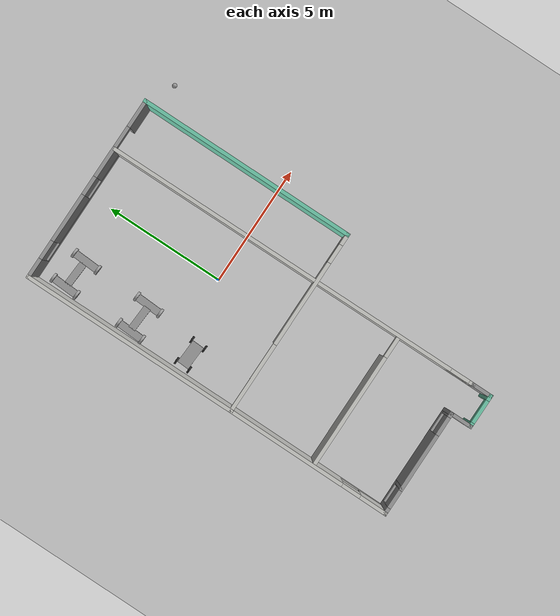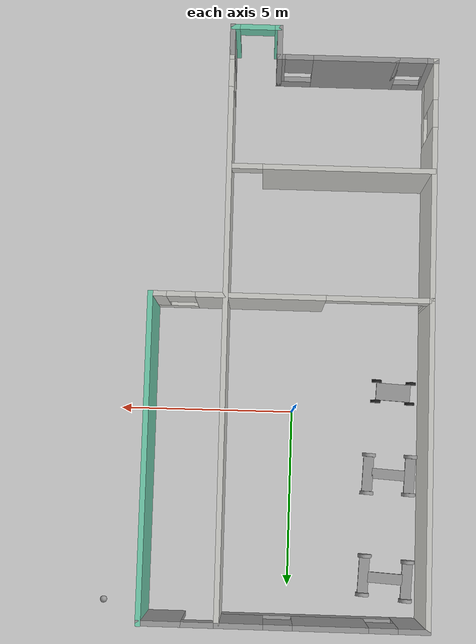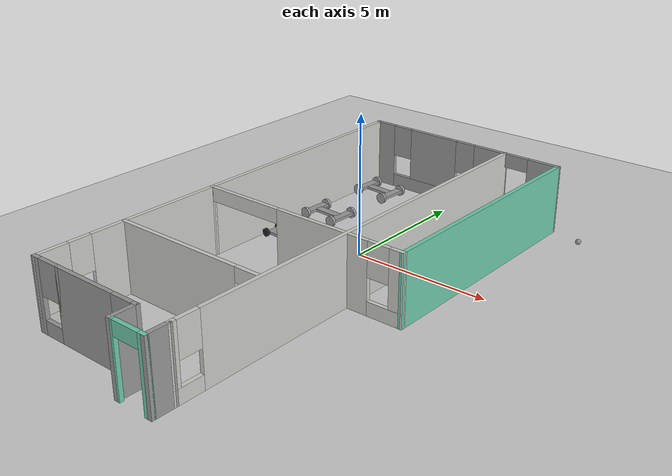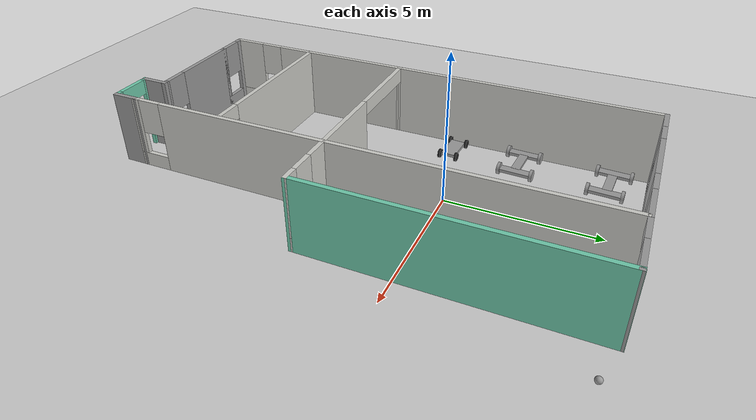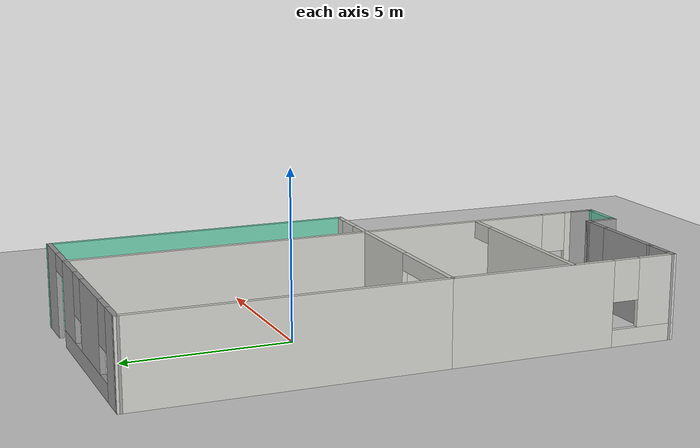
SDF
<sdf version="1.6">
 <world name="default">
  <light name="sun" type="directional">
   <pose>0 0 10 0 -0 0</pose>
   <diffuse>0.8 0.8 0.8 1</diffuse>
   <specular>0.2 0.2 0.2 1</specular>
   <attenuation>
    <range>1000</range>
    <constant>0.9</constant>
    <linear>0.01</linear>
    <quadratic>0.001</quadratic>
   </attenuation>
   <direction>-0.5 0.1 -0.9</direction>
  </light>
  <model name="ground_plane">
   <static>1</static>
   <link name="link">
    <collision name="collision">
     <geometry><plane><normal>0 0 1</normal><size>100 100</size></plane></geometry>
     <surface>
      <contact><collide_bitmask>65535</collide_bitmask></contact>
      <friction><ode><mu>100</mu><mu2>50</mu2></ode></friction>
     </surface>
    </collision>
    <visual name="visual">
     <cast_shadows>0</cast_shadows>
     <geometry><plane><normal>0 0 1</normal><size>100 100</size></plane></geometry>
     <material>
      <script><uri>file://media/materials/scripts/gazebo.material</uri><name>Gazebo/Grey</name></script>
     </material>
    </visual>
   </link>
  </model>
  <gravity>0 0 -9.8</gravity>
  <magnetic_field>6e-06 2.3e-05 -4.2e-05</magnetic_field>
  <atmosphere type="adiabatic"/>
  <physics name="default_physics" default="0" type="ode">
   <max_step_size>0.001</max_step_size>
   <real_time_factor>1</real_time_factor>
   <real_time_update_rate>1000</real_time_update_rate>
  </physics>
  <scene><ambient>0.4 0.4 0.4 1</ambient><background>0.7 0.7 0.7 1</background><shadows>1</shadows></scene>
  <spherical_coordinates>
   <surface_model>EARTH_WGS84</surface_model>
   <latitude_deg>0</latitude_deg>
   <longitude_deg>0</longitude_deg>
   <elevation>0</elevation>
   <heading_deg>0</heading_deg>
  </spherical_coordinates>
  <model name="robot">
   <link name="link_0">
    <pose>-0.676954 1.78805 0.013333 0 -0 0</pose>
    <inertial>
     <mass>1</mass>
     <inertia>
      <ixx>0.166667</ixx>
      <ixy>0</ixy>
      <ixz>0</ixz>
      <iyy>0.166667</iyy>
      <iyz>0</iyz>
      <izz>0.166667</izz>
     </inertia>
    </inertial>
    <visual name="visual">
     <geometry><box><size>0.3 1 0.1</size></box></geometry>
     <material>
      <lighting>1</lighting>
      <script><uri>file://media/materials/scripts/gazebo.material</uri><name>Gazebo/Grey</name></script>
      <shader type="pixel"><normal_map>__default__</normal_map></shader>
      <ambient>0.3 0.3 0.3 1</ambient>
      <diffuse>0.7 0.7 0.7 1</diffuse>
      <specular>0.01 0.01 0.01 1</specular>
      <emissive>0 0 0 1</emissive>
     </material>
    </visual>
    <collision name="collision">
     <geometry><box><size>0.3 1 0.1</size></box></geometry>
     <surface>
      <friction>
       <ode><mu>1</mu><mu2>1</mu2><fdir1>0 0 0</fdir1><slip1>0</slip1><slip2>0</slip2></ode>
       <torsional>
        <coefficient>1</coefficient>
        <patch_radius>0</patch_radius>
        <surface_radius>0</surface_radius>
        <use_patch_radius>1</use_patch_radius>
        <ode><slip>0</slip></ode>
       </torsional>
      </friction>
      <bounce><restitution_coefficient>0</restitution_coefficient><threshold>1e+06</threshold></bounce>
      <contact>
       <collide_without_contact>0</collide_without_contact>
       <collide_without_contact_bitmask>1</collide_without_contact_bitmask>
       <collide_bitmask>1</collide_bitmask>
       <ode>
        <soft_cfm>0</soft_cfm>
        <soft_erp>0.2</soft_erp>
        <kp>1e+13</kp>
        <kd>1</kd>
        <max_vel>0.01</max_vel>
        <min_depth>0</min_depth>
       </ode>
       <bullet>
        <split_impulse>1</split_impulse>
        <split_impulse_penetration_threshold>-0.01</split_impulse_penetration_threshold>
        <soft_cfm>0</soft_cfm>
        <soft_erp>0.2</soft_erp>
        <kp>1e+13</kp>
        <kd>1</kd>
       </bullet>
      </contact>
     </surface>
    </collision>
   </link>
   <link name="link_0_clone">
    <pose>0.57454 1.70519 0.013333 0 -0 0</pose>
    <inertial>
     <mass>1</mass>
     <inertia>
      <ixx>0.166667</ixx>
      <ixy>0</ixy>
      <ixz>0</ixz>
      <iyy>0.166667</iyy>
      <iyz>0</iyz>
      <izz>0.166667</izz>
     </inertia>
    </inertial>
    <visual name="visual">
     <geometry><box><size>0.3 1 0.1</size></box></geometry>
     <material>
      <lighting>1</lighting>
      <script><uri>file://media/materials/scripts/gazebo.material</uri><name>Gazebo/Grey</name></script>
      <shader type="pixel"><normal_map>__default__</normal_map></shader>
      <ambient>0.3 0.3 0.3 1</ambient>
      <diffuse>0.7 0.7 0.7 1</diffuse>
      <specular>0.01 0.01 0.01 1</specular>
      <emissive>0 0 0 1</emissive>
     </material>
    </visual>
    <collision name="collision">
     <geometry><box><size>0.3 1 0.1</size></box></geometry>
     <surface>
      <friction>
       <ode><mu>1</mu><mu2>1</mu2><fdir1>0 0 0</fdir1><slip1>0</slip1><slip2>0</slip2></ode>
       <torsional>
        <coefficient>1</coefficient>
        <patch_radius>0</patch_radius>
        <surface_radius>0</surface_radius>
        <use_patch_radius>1</use_patch_radius>
        <ode><slip>0</slip></ode>
       </torsional>
      </friction>
      <bounce><restitution_coefficient>0</restitution_coefficient><threshold>1e+06</threshold></bounce>
      <contact>
       <collide_without_contact>0</collide_without_contact>
       <collide_without_contact_bitmask>1</collide_without_contact_bitmask>
       <collide_bitmask>1</collide_bitmask>
       <ode>
        <soft_cfm>0</soft_cfm>
        <soft_erp>0.2</soft_erp>
        <kp>1e+13</kp>
        <kd>1</kd>
        <max_vel>0.01</max_vel>
        <min_depth>0</min_depth>
       </ode>
       <bullet>
        <split_impulse>1</split_impulse>
        <split_impulse_penetration_threshold>-0.01</split_impulse_penetration_threshold>
        <soft_cfm>0</soft_cfm>
        <soft_erp>0.2</soft_erp>
        <kp>1e+13</kp>
        <kd>1</kd>
       </bullet>
      </contact>
     </surface>
    </collision>
   </link>
   <link name="link_0_clone_0">
    <pose>-0.051174 1.74887 0.013333 0 0 -1.58141</pose>
    <inertial>
     <mass>1</mass>
     <inertia>
      <ixx>0.166667</ixx>
      <ixy>0</ixy>
      <ixz>0</ixz>
      <iyy>0.166667</iyy>
      <iyz>0</iyz>
      <izz>0.166667</izz>
     </inertia>
    </inertial>
    <visual name="visual">
     <geometry><box><size>0.3 1 0.1</size></box></geometry>
     <material>
      <lighting>1</lighting>
      <script><uri>file://media/materials/scripts/gazebo.material</uri><name>Gazebo/Grey</name></script>
      <shader type="pixel"><normal_map>__default__</normal_map></shader>
      <ambient>0.3 0.3 0.3 1</ambient>
      <diffuse>0.7 0.7 0.7 1</diffuse>
      <specular>0.01 0.01 0.01 1</specular>
      <emissive>0 0 0 1</emissive>
     </material>
    </visual>
    <collision name="collision">
     <geometry><box><size>0.3 1 0.1</size></box></geometry>
     <surface>
      <friction>
       <ode><mu>1</mu><mu2>1</mu2><fdir1>0 0 0</fdir1><slip1>0</slip1><slip2>0</slip2></ode>
       <torsional>
        <coefficient>1</coefficient>
        <patch_radius>0</patch_radius>
        <surface_radius>0</surface_radius>
        <use_patch_radius>1</use_patch_radius>
        <ode><slip>0</slip></ode>
       </torsional>
      </friction>
      <bounce><restitution_coefficient>0</restitution_coefficient><threshold>1e+06</threshold></bounce>
      <contact>
       <collide_without_contact>0</collide_without_contact>
       <collide_without_contact_bitmask>1</collide_without_contact_bitmask>
       <collide_bitmask>1</collide_bitmask>
       <ode>
        <soft_cfm>0</soft_cfm>
        <soft_erp>0.2</soft_erp>
        <kp>1e+13</kp>
        <kd>1</kd>
        <max_vel>0.01</max_vel>
        <min_depth>0</min_depth>
       </ode>
       <bullet>
        <split_impulse>1</split_impulse>
        <split_impulse_penetration_threshold>-0.01</split_impulse_penetration_threshold>
        <soft_cfm>0</soft_cfm>
        <soft_erp>0.2</soft_erp>
        <kp>1e+13</kp>
        <kd>1</kd>
       </bullet>
      </contact>
     </surface>
    </collision>
   </link>
   <link name="link_0_clone_0_clone">
    <pose>0.037632 -1.23361 0.013333 0 0 -1.58141</pose>
    <inertial>
     <mass>1</mass>
     <inertia>
      <ixx>0.166667</ixx>
      <ixy>0</ixy>
      <ixz>0</ixz>
      <iyy>0.166667</iyy>
      <iyz>0</iyz>
      <izz>0.166667</izz>
     </inertia>
    </inertial>
    <visual name="visual">
     <geometry><box><size>0.3 1 0.1</size></box></geometry>
     <material>
      <lighting>1</lighting>
      <script><uri>file://media/materials/scripts/gazebo.material</uri><name>Gazebo/Grey</name></script>
      <shader type="pixel"><normal_map>__default__</normal_map></shader>
      <ambient>0.3 0.3 0.3 1</ambient>
      <diffuse>0.7 0.7 0.7 1</diffuse>
      <specular>0.01 0.01 0.01 1</specular>
      <emissive>0 0 0 1</emissive>
     </material>
    </visual>
    <collision name="collision">
     <geometry><box><size>0.3 1 0.1</size></box></geometry>
     <surface>
      <friction>
       <ode><mu>1</mu><mu2>1</mu2><fdir1>0 0 0</fdir1><slip1>0</slip1><slip2>0</slip2></ode>
       <torsional>
        <coefficient>1</coefficient>
        <patch_radius>0</patch_radius>
        <surface_radius>0</surface_radius>
        <use_patch_radius>1</use_patch_radius>
        <ode><slip>0</slip></ode>
       </torsional>
      </friction>
      <bounce><restitution_coefficient>0</restitution_coefficient><threshold>1e+06</threshold></bounce>
      <contact>
       <collide_without_contact>0</collide_without_contact>
       <collide_without_contact_bitmask>1</collide_without_contact_bitmask>
       <collide_bitmask>1</collide_bitmask>
       <ode>
        <soft_cfm>0</soft_cfm>
        <soft_erp>0.2</soft_erp>
        <kp>1e+13</kp>
        <kd>1</kd>
        <max_vel>0.01</max_vel>
        <min_depth>0</min_depth>
       </ode>
       <bullet>
        <split_impulse>1</split_impulse>
        <split_impulse_penetration_threshold>-0.01</split_impulse_penetration_threshold>
        <soft_cfm>0</soft_cfm>
        <soft_erp>0.2</soft_erp>
        <kp>1e+13</kp>
        <kd>1</kd>
       </bullet>
      </contact>
     </surface>
    </collision>
   </link>
   <link name="link_0_clone_0_clone_0">
    <pose>0.651785 -1.20871 0.013333 0 0 -3.13736</pose>
    <inertial>
     <mass>1</mass>
     <inertia>
      <ixx>0.166667</ixx>
      <ixy>0</ixy>
      <ixz>0</ixz>
      <iyy>0.166667</iyy>
      <iyz>0</iyz>
      <izz>0.166667</izz>
     </inertia>
    </inertial>
    <visual name="visual">
     <geometry><box><size>0.3 1 0.1</size></box></geometry>
     <material>
      <lighting>1</lighting>
      <script><uri>file://media/materials/scripts/gazebo.material</uri><name>Gazebo/Grey</name></script>
      <shader type="pixel"><normal_map>__default__</normal_map></shader>
      <ambient>0.3 0.3 0.3 1</ambient>
      <diffuse>0.7 0.7 0.7 1</diffuse>
      <specular>0.01 0.01 0.01 1</specular>
      <emissive>0 0 0 1</emissive>
     </material>
    </visual>
    <collision name="collision">
     <geometry><box><size>0.3 1 0.1</size></box></geometry>
     <surface>
      <friction>
       <ode><mu>1</mu><mu2>1</mu2><fdir1>0 0 0</fdir1><slip1>0</slip1><slip2>0</slip2></ode>
       <torsional>
        <coefficient>1</coefficient>
        <patch_radius>0</patch_radius>
        <surface_radius>0</surface_radius>
        <use_patch_radius>1</use_patch_radius>
        <ode><slip>0</slip></ode>
       </torsional>
      </friction>
      <bounce><restitution_coefficient>0</restitution_coefficient><threshold>1e+06</threshold></bounce>
      <contact>
       <collide_without_contact>0</collide_without_contact>
       <collide_without_contact_bitmask>1</collide_without_contact_bitmask>
       <collide_bitmask>1</collide_bitmask>
       <ode>
        <soft_cfm>0</soft_cfm>
        <soft_erp>0.2</soft_erp>
        <kp>1e+13</kp>
        <kd>1</kd>
        <max_vel>0.01</max_vel>
        <min_depth>0</min_depth>
       </ode>
       <bullet>
        <split_impulse>1</split_impulse>
        <split_impulse_penetration_threshold>-0.01</split_impulse_penetration_threshold>
        <soft_cfm>0</soft_cfm>
        <soft_erp>0.2</soft_erp>
        <kp>1e+13</kp>
        <kd>1</kd>
       </bullet>
      </contact>
     </surface>
    </collision>
   </link>
   <link name="link_0_clone_0_clone_1">
    <pose>-0.568566 -1.24292 0.013333 0 0 -3.13728</pose>
    <inertial>
     <mass>1</mass>
     <inertia>
      <ixx>0.166667</ixx>
      <ixy>0</ixy>
      <ixz>0</ixz>
      <iyy>0.166667</iyy>
      <iyz>0</iyz>
      <izz>0.166667</izz>
     </inertia>
    </inertial>
    <visual name="visual">
     <geometry><box><size>0.3 1 0.1</size></box></geometry>
     <material>
      <lighting>1</lighting>
      <script><uri>file://media/materials/scripts/gazebo.material</uri><name>Gazebo/Grey</name></script>
      <shader type="pixel"><normal_map>__default__</normal_map></shader>
      <ambient>0.3 0.3 0.3 1</ambient>
      <diffuse>0.7 0.7 0.7 1</diffuse>
      <specular>0.01 0.01 0.01 1</specular>
      <emissive>0 0 0 1</emissive>
     </material>
    </visual>
    <collision name="collision">
     <geometry><box><size>0.3 1 0.1</size></box></geometry>
     <surface>
      <friction>
       <ode><mu>1</mu><mu2>1</mu2><fdir1>0 0 0</fdir1><slip1>0</slip1><slip2>0</slip2></ode>
       <torsional>
        <coefficient>1</coefficient>
        <patch_radius>0</patch_radius>
        <surface_radius>0</surface_radius>
        <use_patch_radius>1</use_patch_radius>
        <ode><slip>0</slip></ode>
       </torsional>
      </friction>
      <bounce><restitution_coefficient>0</restitution_coefficient><threshold>1e+06</threshold></bounce>
      <contact>
       <collide_without_contact>0</collide_without_contact>
       <collide_without_contact_bitmask>1</collide_without_contact_bitmask>
       <collide_bitmask>1</collide_bitmask>
       <ode>
        <soft_cfm>0</soft_cfm>
        <soft_erp>0.2</soft_erp>
        <kp>1e+13</kp>
        <kd>1</kd>
        <max_vel>0.01</max_vel>
        <min_depth>0</min_depth>
       </ode>
       <bullet>
        <split_impulse>1</split_impulse>
        <split_impulse_penetration_threshold>-0.01</split_impulse_penetration_threshold>
        <soft_cfm>0</soft_cfm>
        <soft_erp>0.2</soft_erp>
        <kp>1e+13</kp>
        <kd>1</kd>
       </bullet>
      </contact>
     </surface>
    </collision>
   </link>
   <link name="link_1">
    <pose>0.57454 1.15517 0.013333 1.5707 -0 0</pose>
    <inertial>
     <mass>1</mass>
     <inertia><ixx>0.145833</ixx><ixy>0</ixy><ixz>0</ixz><iyy>0.145833</iyy><iyz>0</iyz><izz>0.125</izz></inertia>
    </inertial>
    <visual name="visual">
     <geometry><cylinder><radius>0.2</radius><length>0.1</length></cylinder></geometry>
     <material>
      <lighting>1</lighting>
      <script><uri>file://media/materials/scripts/gazebo.material</uri><name>Gazebo/Grey</name></script>
      <shader type="pixel"><normal_map>__default__</normal_map></shader>
      <ambient>0.3 0.3 0.3 1</ambient>
      <diffuse>0.7 0.7 0.7 1</diffuse>
      <specular>0.01 0.01 0.01 1</specular>
      <emissive>0 0 0 1</emissive>
     </material>
    </visual>
    <collision name="collision">
     <geometry><cylinder><radius>0.2</radius><length>0.1</length></cylinder></geometry>
     <surface>
      <friction>
       <ode><mu>1</mu><mu2>1</mu2><fdir1>0 0 0</fdir1><slip1>0</slip1><slip2>0</slip2></ode>
       <torsional>
        <coefficient>1</coefficient>
        <patch_radius>0</patch_radius>
        <surface_radius>0</surface_radius>
        <use_patch_radius>1</use_patch_radius>
        <ode><slip>0</slip></ode>
       </torsional>
      </friction>
      <bounce><restitution_coefficient>0</restitution_coefficient><threshold>1e+06</threshold></bounce>
      <contact>
       <collide_without_contact>0</collide_without_contact>
       <collide_without_contact_bitmask>1</collide_without_contact_bitmask>
       <collide_bitmask>1</collide_bitmask>
       <ode>
        <soft_cfm>0</soft_cfm>
        <soft_erp>0.2</soft_erp>
        <kp>1e+13</kp>
        <kd>1</kd>
        <max_vel>0.01</max_vel>
        <min_depth>0</min_depth>
       </ode>
       <bullet>
        <split_impulse>1</split_impulse>
        <split_impulse_penetration_threshold>-0.01</split_impulse_penetration_threshold>
        <soft_cfm>0</soft_cfm>
        <soft_erp>0.2</soft_erp>
        <kp>1e+13</kp>
        <kd>1</kd>
       </bullet>
      </contact>
     </surface>
    </collision>
   </link>
   <link name="link_1_clone">
    <pose>-0.676954 2.33807 0.013333 1.5707 -0 0</pose>
    <inertial>
     <mass>1</mass>
     <inertia><ixx>0.145833</ixx><ixy>0</ixy><ixz>0</ixz><iyy>0.145833</iyy><iyz>0</iyz><izz>0.125</izz></inertia>
    </inertial>
    <visual name="visual">
     <geometry><cylinder><radius>0.2</radius><length>0.1</length></cylinder></geometry>
     <material>
      <lighting>1</lighting>
      <script><uri>file://media/materials/scripts/gazebo.material</uri><name>Gazebo/Grey</name></script>
      <shader type="pixel"><normal_map>__default__</normal_map></shader>
      <ambient>0.3 0.3 0.3 1</ambient>
      <diffuse>0.7 0.7 0.7 1</diffuse>
      <specular>0.01 0.01 0.01 1</specular>
      <emissive>0 0 0 1</emissive>
     </material>
    </visual>
    <collision name="collision">
     <geometry><cylinder><radius>0.2</radius><length>0.1</length></cylinder></geometry>
     <surface>
      <friction>
       <ode><mu>1</mu><mu2>1</mu2><fdir1>0 0 0</fdir1><slip1>0</slip1><slip2>0</slip2></ode>
       <torsional>
        <coefficient>1</coefficient>
        <patch_radius>0</patch_radius>
        <surface_radius>0</surface_radius>
        <use_patch_radius>1</use_patch_radius>
        <ode><slip>0</slip></ode>
       </torsional>
      </friction>
      <bounce><restitution_coefficient>0</restitution_coefficient><threshold>1e+06</threshold></bounce>
      <contact>
       <collide_without_contact>0</collide_without_contact>
       <collide_without_contact_bitmask>1</collide_without_contact_bitmask>
       <collide_bitmask>1</collide_bitmask>
       <ode>
        <soft_cfm>0</soft_cfm>
        <soft_erp>0.2</soft_erp>
        <kp>1e+13</kp>
        <kd>1</kd>
        <max_vel>0.01</max_vel>
        <min_depth>0</min_depth>
       </ode>
       <bullet>
        <split_impulse>1</split_impulse>
        <split_impulse_penetration_threshold>-0.01</split_impulse_penetration_threshold>
        <soft_cfm>0</soft_cfm>
        <soft_erp>0.2</soft_erp>
        <kp>1e+13</kp>
        <kd>1</kd>
       </bullet>
      </contact>
     </surface>
    </collision>
   </link>
   <link name="link_1_clone_0">
    <pose>0.651785 -1.75936 0.013333 1.5707 -0 0</pose>
    <inertial>
     <mass>1</mass>
     <inertia><ixx>0.145833</ixx><ixy>0</ixy><ixz>0</ixz><iyy>0.145833</iyy><iyz>0</iyz><izz>0.125</izz></inertia>
    </inertial>
    <visual name="visual">
     <geometry><cylinder><radius>0.2</radius><length>0.1</length></cylinder></geometry>
     <material>
      <lighting>1</lighting>
      <script><uri>file://media/materials/scripts/gazebo.material</uri><name>Gazebo/Grey</name></script>
      <shader type="pixel"><normal_map>__default__</normal_map></shader>
      <ambient>0.3 0.3 0.3 1</ambient>
      <diffuse>0.7 0.7 0.7 1</diffuse>
      <specular>0.01 0.01 0.01 1</specular>
      <emissive>0 0 0 1</emissive>
     </material>
    </visual>
    <collision name="collision">
     <geometry><cylinder><radius>0.2</radius><length>0.1</length></cylinder></geometry>
     <surface>
      <friction>
       <ode><mu>1</mu><mu2>1</mu2><fdir1>0 0 0</fdir1><slip1>0</slip1><slip2>0</slip2></ode>
       <torsional>
        <coefficient>1</coefficient>
        <patch_radius>0</patch_radius>
        <surface_radius>0</surface_radius>
        <use_patch_radius>1</use_patch_radius>
        <ode><slip>0</slip></ode>
       </torsional>
      </friction>
      <bounce><restitution_coefficient>0</restitution_coefficient><threshold>1e+06</threshold></bounce>
      <contact>
       <collide_without_contact>0</collide_without_contact>
       <collide_without_contact_bitmask>1</collide_without_contact_bitmask>
       <collide_bitmask>1</collide_bitmask>
       <ode>
        <soft_cfm>0</soft_cfm>
        <soft_erp>0.2</soft_erp>
        <kp>1e+13</kp>
        <kd>1</kd>
        <max_vel>0.01</max_vel>
        <min_depth>0</min_depth>
       </ode>
       <bullet>
        <split_impulse>1</split_impulse>
        <split_impulse_penetration_threshold>-0.01</split_impulse_penetration_threshold>
        <soft_cfm>0</soft_cfm>
        <soft_erp>0.2</soft_erp>
        <kp>1e+13</kp>
        <kd>1</kd>
       </bullet>
      </contact>
     </surface>
    </collision>
   </link>
   <link name="link_1_clone_1">
    <pose>-0.676954 1.23803 0.013333 1.5707 -0 0</pose>
    <inertial>
     <mass>1</mass>
     <inertia><ixx>0.145833</ixx><ixy>0</ixy><ixz>0</ixz><iyy>0.145833</iyy><iyz>0</iyz><izz>0.125</izz></inertia>
    </inertial>
    <visual name="visual">
     <geometry><cylinder><radius>0.2</radius><length>0.1</length></cylinder></geometry>
     <material>
      <lighting>1</lighting>
      <script><uri>file://media/materials/scripts/gazebo.material</uri><name>Gazebo/Grey</name></script>
      <shader type="pixel"><normal_map>__default__</normal_map></shader>
      <ambient>0.3 0.3 0.3 1</ambient>
      <diffuse>0.7 0.7 0.7 1</diffuse>
      <specular>0.01 0.01 0.01 1</specular>
      <emissive>0 0 0 1</emissive>
     </material>
    </visual>
    <collision name="collision">
     <geometry><cylinder><radius>0.2</radius><length>0.1</length></cylinder></geometry>
     <surface>
      <friction>
       <ode><mu>1</mu><mu2>1</mu2><fdir1>0 0 0</fdir1><slip1>0</slip1><slip2>0</slip2></ode>
       <torsional>
        <coefficient>1</coefficient>
        <patch_radius>0</patch_radius>
        <surface_radius>0</surface_radius>
        <use_patch_radius>1</use_patch_radius>
        <ode><slip>0</slip></ode>
       </torsional>
      </friction>
      <bounce><restitution_coefficient>0</restitution_coefficient><threshold>1e+06</threshold></bounce>
      <contact>
       <collide_without_contact>0</collide_without_contact>
       <collide_without_contact_bitmask>1</collide_without_contact_bitmask>
       <collide_bitmask>1</collide_bitmask>
       <ode>
        <soft_cfm>0</soft_cfm>
        <soft_erp>0.2</soft_erp>
        <kp>1e+13</kp>
        <kd>1</kd>
        <max_vel>0.01</max_vel>
        <min_depth>0</min_depth>
       </ode>
       <bullet>
        <split_impulse>1</split_impulse>
        <split_impulse_penetration_threshold>-0.01</split_impulse_penetration_threshold>
        <soft_cfm>0</soft_cfm>
        <soft_erp>0.2</soft_erp>
        <kp>1e+13</kp>
        <kd>1</kd>
       </bullet>
      </contact>
     </surface>
    </collision>
   </link>
   <link name="link_1_clone_1_clone">
    <pose>0.57454 2.25521 0.013333 1.5707 -0 0</pose>
    <inertial>
     <mass>1</mass>
     <inertia><ixx>0.145833</ixx><ixy>0</ixy><ixz>0</ixz><iyy>0.145833</iyy><iyz>0</iyz><izz>0.125</izz></inertia>
    </inertial>
    <visual name="visual">
     <geometry><cylinder><radius>0.2</radius><length>0.1</length></cylinder></geometry>
     <material>
      <lighting>1</lighting>
      <script><uri>file://media/materials/scripts/gazebo.material</uri><name>Gazebo/Grey</name></script>
      <shader type="pixel"><normal_map>__default__</normal_map></shader>
      <ambient>0.3 0.3 0.3 1</ambient>
      <diffuse>0.7 0.7 0.7 1</diffuse>
      <specular>0.01 0.01 0.01 1</specular>
      <emissive>0 0 0 1</emissive>
     </material>
    </visual>
    <collision name="collision">
     <geometry><cylinder><radius>0.2</radius><length>0.1</length></cylinder></geometry>
     <surface>
      <friction>
       <ode><mu>1</mu><mu2>1</mu2><fdir1>0 0 0</fdir1><slip1>0</slip1><slip2>0</slip2></ode>
       <torsional>
        <coefficient>1</coefficient>
        <patch_radius>0</patch_radius>
        <surface_radius>0</surface_radius>
        <use_patch_radius>1</use_patch_radius>
        <ode><slip>0</slip></ode>
       </torsional>
      </friction>
      <bounce><restitution_coefficient>0</restitution_coefficient><threshold>1e+06</threshold></bounce>
      <contact>
       <collide_without_contact>0</collide_without_contact>
       <collide_without_contact_bitmask>1</collide_without_contact_bitmask>
       <collide_bitmask>1</collide_bitmask>
       <ode>
        <soft_cfm>0</soft_cfm>
        <soft_erp>0.2</soft_erp>
        <kp>1e+13</kp>
        <kd>1</kd>
        <max_vel>0.01</max_vel>
        <min_depth>0</min_depth>
       </ode>
       <bullet>
        <split_impulse>1</split_impulse>
        <split_impulse_penetration_threshold>-0.01</split_impulse_penetration_threshold>
        <soft_cfm>0</soft_cfm>
        <soft_erp>0.2</soft_erp>
        <kp>1e+13</kp>
        <kd>1</kd>
       </bullet>
      </contact>
     </surface>
    </collision>
   </link>
   <link name="link_1_clone_2">
    <pose>-0.568566 -1.79358 0.013333 1.5707 -0 0</pose>
    <inertial>
     <mass>1</mass>
     <inertia><ixx>0.145833</ixx><ixy>0</ixy><ixz>0</ixz><iyy>0.145833</iyy><iyz>0</iyz><izz>0.125</izz></inertia>
    </inertial>
    <visual name="visual">
     <geometry><cylinder><radius>0.2</radius><length>0.1</length></cylinder></geometry>
     <material>
      <lighting>1</lighting>
      <script><uri>file://media/materials/scripts/gazebo.material</uri><name>Gazebo/Grey</name></script>
      <shader type="pixel"><normal_map>__default__</normal_map></shader>
      <ambient>0.3 0.3 0.3 1</ambient>
      <diffuse>0.7 0.7 0.7 1</diffuse>
      <specular>0.01 0.01 0.01 1</specular>
      <emissive>0 0 0 1</emissive>
     </material>
    </visual>
    <collision name="collision">
     <geometry><cylinder><radius>0.2</radius><length>0.1</length></cylinder></geometry>
     <surface>
      <friction>
       <ode><mu>1</mu><mu2>1</mu2><fdir1>0 0 0</fdir1><slip1>0</slip1><slip2>0</slip2></ode>
       <torsional>
        <coefficient>1</coefficient>
        <patch_radius>0</patch_radius>
        <surface_radius>0</surface_radius>
        <use_patch_radius>1</use_patch_radius>
        <ode><slip>0</slip></ode>
       </torsional>
      </friction>
      <bounce><restitution_coefficient>0</restitution_coefficient><threshold>1e+06</threshold></bounce>
      <contact>
       <collide_without_contact>0</collide_without_contact>
       <collide_without_contact_bitmask>1</collide_without_contact_bitmask>
       <collide_bitmask>1</collide_bitmask>
       <ode>
        <soft_cfm>0</soft_cfm>
        <soft_erp>0.2</soft_erp>
        <kp>1e+13</kp>
        <kd>1</kd>
        <max_vel>0.01</max_vel>
        <min_depth>0</min_depth>
       </ode>
       <bullet>
        <split_impulse>1</split_impulse>
        <split_impulse_penetration_threshold>-0.01</split_impulse_penetration_threshold>
        <soft_cfm>0</soft_cfm>
        <soft_erp>0.2</soft_erp>
        <kp>1e+13</kp>
        <kd>1</kd>
       </bullet>
      </contact>
     </surface>
    </collision>
   </link>
   <link name="link_1_clone_3">
    <pose>0.651785 -0.658058 0.013333 1.5707 -0 0</pose>
    <inertial>
     <mass>1</mass>
     <inertia><ixx>0.145833</ixx><ixy>0</ixy><ixz>0</ixz><iyy>0.145833</iyy><iyz>0</iyz><izz>0.125</izz></inertia>
    </inertial>
    <visual name="visual">
     <geometry><cylinder><radius>0.2</radius><length>0.1</length></cylinder></geometry>
     <material>
      <lighting>1</lighting>
      <script><uri>file://media/materials/scripts/gazebo.material</uri><name>Gazebo/Grey</name></script>
      <shader type="pixel"><normal_map>__default__</normal_map></shader>
      <ambient>0.3 0.3 0.3 1</ambient>
      <diffuse>0.7 0.7 0.7 1</diffuse>
      <specular>0.01 0.01 0.01 1</specular>
      <emissive>0 0 0 1</emissive>
     </material>
    </visual>
    <collision name="collision">
     <geometry><cylinder><radius>0.2</radius><length>0.1</length></cylinder></geometry>
     <surface>
      <friction>
       <ode><mu>1</mu><mu2>1</mu2><fdir1>0 0 0</fdir1><slip1>0</slip1><slip2>0</slip2></ode>
       <torsional>
        <coefficient>1</coefficient>
        <patch_radius>0</patch_radius>
        <surface_radius>0</surface_radius>
        <use_patch_radius>1</use_patch_radius>
        <ode><slip>0</slip></ode>
       </torsional>
      </friction>
      <bounce><restitution_coefficient>0</restitution_coefficient><threshold>1e+06</threshold></bounce>
      <contact>
       <collide_without_contact>0</collide_without_contact>
       <collide_without_contact_bitmask>1</collide_without_contact_bitmask>
       <collide_bitmask>1</collide_bitmask>
       <ode>
        <soft_cfm>0</soft_cfm>
        <soft_erp>0.2</soft_erp>
        <kp>1e+13</kp>
        <kd>1</kd>
        <max_vel>0.01</max_vel>
        <min_depth>0</min_depth>
       </ode>
       <bullet>
        <split_impulse>1</split_impulse>
        <split_impulse_penetration_threshold>-0.01</split_impulse_penetration_threshold>
        <soft_cfm>0</soft_cfm>
        <soft_erp>0.2</soft_erp>
        <kp>1e+13</kp>
        <kd>1</kd>
       </bullet>
      </contact>
     </surface>
    </collision>
   </link>
   <link name="link_1_clone_4">
    <pose>-0.568566 -0.692256 0.013333 1.5707 -0 0</pose>
    <inertial>
     <mass>1</mass>
     <inertia><ixx>0.145833</ixx><ixy>0</ixy><ixz>0</ixz><iyy>0.145833</iyy><iyz>0</iyz><izz>0.125</izz></inertia>
    </inertial>
    <visual name="visual">
     <geometry><cylinder><radius>0.2</radius><length>0.1</length></cylinder></geometry>
     <material>
      <lighting>1</lighting>
      <script><uri>file://media/materials/scripts/gazebo.material</uri><name>Gazebo/Grey</name></script>
      <shader type="pixel"><normal_map>__default__</normal_map></shader>
      <ambient>0.3 0.3 0.3 1</ambient>
      <diffuse>0.7 0.7 0.7 1</diffuse>
      <specular>0.01 0.01 0.01 1</specular>
      <emissive>0 0 0 1</emissive>
     </material>
    </visual>
    <collision name="collision">
     <geometry><cylinder><radius>0.2</radius><length>0.1</length></cylinder></geometry>
     <surface>
      <friction>
       <ode><mu>1</mu><mu2>1</mu2><fdir1>0 0 0</fdir1><slip1>0</slip1><slip2>0</slip2></ode>
       <torsional>
        <coefficient>1</coefficient>
        <patch_radius>0</patch_radius>
        <surface_radius>0</surface_radius>
        <use_patch_radius>1</use_patch_radius>
        <ode><slip>0</slip></ode>
       </torsional>
      </friction>
      <bounce><restitution_coefficient>0</restitution_coefficient><threshold>1e+06</threshold></bounce>
      <contact>
       <collide_without_contact>0</collide_without_contact>
       <collide_without_contact_bitmask>1</collide_without_contact_bitmask>
       <collide_bitmask>1</collide_bitmask>
       <ode>
        <soft_cfm>0</soft_cfm>
        <soft_erp>0.2</soft_erp>
        <kp>1e+13</kp>
        <kd>1</kd>
        <max_vel>0.01</max_vel>
        <min_depth>0</min_depth>
       </ode>
       <bullet>
        <split_impulse>1</split_impulse>
        <split_impulse_penetration_threshold>-0.01</split_impulse_penetration_threshold>
        <soft_cfm>0</soft_cfm>
        <soft_erp>0.2</soft_erp>
        <kp>1e+13</kp>
        <kd>1</kd>
       </bullet>
      </contact>
     </surface>
    </collision>
   </link>
   <model name="cart_front_steer">
    <link name="chassis">
     <pose>0 0 0.15 0 -0 0</pose>
     <inertial>
      <pose>0.1 0 0 0 -0 0</pose>
      <mass>10</mass>
      <inertia>
       <ixx>0.216667</ixx>
       <iyy>0.841667</iyy>
       <izz>1.04167</izz>
       <ixy>0</ixy>
       <ixz>0</ixz>
       <iyz>0</iyz>
      </inertia>
     </inertial>
     <collision name="collision"><geometry><box><size>1 0.5 0.1</size></box></geometry></collision>
     <visual name="visual">
      <geometry><box><size>1 0.5 0.1</size></box></geometry>
      <material>
       <script><uri>file://media/materials/scripts/gazebo.material</uri><name>Gazebo/Grey</name></script>
      </material>
     </visual>
    </link>
    <link name="wheel_front_left">
     <pose>0.5 0.298 0.15 -1.5708 -0.087266 0</pose>
     <inertial>
      <mass>0.5</mass>
      <inertia>
       <ixx>0.00307917</ixx>
       <iyy>0.00307917</iyy>
       <izz>0.005625</izz>
       <ixy>0</ixy>
       <ixz>0</ixz>
       <iyz>0</iyz>
      </inertia>
     </inertial>
     <collision name="collision">
      <geometry><cylinder><radius>0.15</radius><length>0.08</length></cylinder></geometry>
     </collision>
     <visual name="visual">
      <geometry><cylinder><radius>0.15</radius><length>0.08</length></cylinder></geometry>
      <material>
       <script><uri>file://media/materials/scripts/gazebo.material</uri><name>Gazebo/Black</name></script>
      </material>
     </visual>
    </link>
    <joint name="wheel_front_left_steer_spin" type="universal">
     <parent>chassis</parent>
     <child>wheel_front_left</child>
     <axis>
      <xyz>0 -1 0</xyz>
      <limit><lower>-0.610865</lower><upper>0.610865</upper></limit>
      <use_parent_model_frame>0</use_parent_model_frame>
      <dynamics><spring_reference>0</spring_reference><spring_stiffness>0</spring_stiffness></dynamics>
     </axis>
     <axis2>
      <xyz>0 0 1</xyz>
      <use_parent_model_frame>0</use_parent_model_frame>
      <dynamics><spring_reference>0</spring_reference><spring_stiffness>0</spring_stiffness></dynamics>
     </axis2>
    </joint>
    <link name="wheel_front_right">
     <pose>0.5 -0.298 0.15 -1.5708 -0.087266 0</pose>
     <inertial>
      <mass>0.5</mass>
      <inertia>
       <ixx>0.00307917</ixx>
       <iyy>0.00307917</iyy>
       <izz>0.005625</izz>
       <ixy>0</ixy>
       <ixz>0</ixz>
       <iyz>0</iyz>
      </inertia>
     </inertial>
     <collision name="collision">
      <geometry><cylinder><radius>0.15</radius><length>0.08</length></cylinder></geometry>
     </collision>
     <visual name="visual">
      <geometry><cylinder><radius>0.15</radius><length>0.08</length></cylinder></geometry>
      <material>
       <script><uri>file://media/materials/scripts/gazebo.material</uri><name>Gazebo/Black</name></script>
      </material>
     </visual>
    </link>
    <joint name="wheel_front_right_steer_spin" type="universal">
     <parent>chassis</parent>
     <child>wheel_front_right</child>
     <axis>
      <xyz>0 -1 0</xyz>
      <limit><lower>-0.610865</lower><upper>0.610865</upper></limit>
      <use_parent_model_frame>0</use_parent_model_frame>
      <dynamics><spring_reference>0</spring_reference><spring_stiffness>0</spring_stiffness></dynamics>
     </axis>
     <axis2>
      <xyz>0 0 1</xyz>
      <use_parent_model_frame>0</use_parent_model_frame>
      <dynamics><spring_reference>0</spring_reference><spring_stiffness>0</spring_stiffness></dynamics>
     </axis2>
    </joint>
    <link name="wheel_rear_left">
     <pose>-0.5 0.298 0.15 -1.5708 0 0</pose>
     <inertial>
      <mass>0.5</mass>
      <inertia>
       <ixx>0.00307917</ixx>
       <iyy>0.00307917</iyy>
       <izz>0.005625</izz>
       <ixy>0</ixy>
       <ixz>0</ixz>
       <iyz>0</iyz>
      </inertia>
     </inertial>
     <collision name="collision">
      <geometry><cylinder><radius>0.15</radius><length>0.08</length></cylinder></geometry>
     </collision>
     <visual name="visual">
      <geometry><cylinder><radius>0.15</radius><length>0.08</length></cylinder></geometry>
      <material>
       <script><uri>file://media/materials/scripts/gazebo.material</uri><name>Gazebo/Black</name></script>
      </material>
     </visual>
    </link>
    <joint name="wheel_rear_left_spin" type="revolute">
     <parent>chassis</parent>
     <child>wheel_rear_left</child>
     <axis>
      <xyz>0 0 1</xyz>
      <use_parent_model_frame>0</use_parent_model_frame>
      <limit><lower>-1e+16</lower><upper>1e+16</upper></limit>
      <dynamics><spring_reference>0</spring_reference><spring_stiffness>0</spring_stiffness></dynamics>
     </axis>
    </joint>
    <link name="wheel_rear_right">
     <pose>-0.5 -0.298 0.15 -1.5708 0 0</pose>
     <inertial>
      <mass>0.5</mass>
      <inertia>
       <ixx>0.00307917</ixx>
       <iyy>0.00307917</iyy>
       <izz>0.005625</izz>
       <ixy>0</ixy>
       <ixz>0</ixz>
       <iyz>0</iyz>
      </inertia>
     </inertial>
     <collision name="collision">
      <geometry><cylinder><radius>0.15</radius><length>0.08</length></cylinder></geometry>
     </collision>
     <visual name="visual">
      <geometry><cylinder><radius>0.15</radius><length>0.08</length></cylinder></geometry>
      <material>
       <script><uri>file://media/materials/scripts/gazebo.material</uri><name>Gazebo/Black</name></script>
      </material>
     </visual>
    </link>
    <joint name="wheel_rear_right_spin" type="revolute">
     <parent>chassis</parent>
     <child>wheel_rear_right</child>
     <axis>
      <xyz>0 0 1</xyz>
      <use_parent_model_frame>0</use_parent_model_frame>
      <limit><lower>-1e+16</lower><upper>1e+16</upper></limit>
      <dynamics><spring_reference>0</spring_reference><spring_stiffness>0</spring_stiffness></dynamics>
     </axis>
    </joint>
    <pose>0.071137 -3.6401 -0.186667 0 -0 0</pose>
   </model>
   <joint name="link_0_JOINT_0" type="fixed">
    <parent>link_0</parent>
    <child>link_0_clone_0</child>
    <physics>
     <ode><limit><cfm>0</cfm><erp>0.2</erp></limit><suspension><cfm>0</cfm><erp>0.2</erp></suspension></ode>
    </physics>
   </joint>
   <joint name="link_0_JOINT_2" type="revolute">
    <parent>link_0</parent>
    <child>link_1_clone_1</child>
    <axis>
     <xyz>0 0 1</xyz>
     <use_parent_model_frame>0</use_parent_model_frame>
     <limit>
      <lower>-1.79769e+308</lower>
      <upper>1.79769e+308</upper>
      <effort>-1</effort>
      <velocity>-1</velocity>
     </limit>
     <dynamics>
      <spring_reference>0</spring_reference>
      <spring_stiffness>0</spring_stiffness>
      <damping>0</damping>
     </dynamics>
    </axis>
    <physics>
     <ode><limit><cfm>0</cfm><erp>0.2</erp></limit><suspension><cfm>0</cfm><erp>0.2</erp></suspension></ode>
    </physics>
   </joint>
   <joint name="link_0_JOINT_3" type="revolute">
    <parent>link_0</parent>
    <child>link_1_clone</child>
    <axis>
     <xyz>0 0 1</xyz>
     <use_parent_model_frame>0</use_parent_model_frame>
     <limit>
      <lower>-1.79769e+308</lower>
      <upper>1.79769e+308</upper>
      <effort>-1</effort>
      <velocity>-1</velocity>
     </limit>
     <dynamics>
      <spring_reference>0</spring_reference>
      <spring_stiffness>0</spring_stiffness>
      <damping>0</damping>
     </dynamics>
    </axis>
    <physics>
     <ode><limit><cfm>0</cfm><erp>0.2</erp></limit><suspension><cfm>0</cfm><erp>0.2</erp></suspension></ode>
    </physics>
   </joint>
   <joint name="link_0_clone_0_JOINT_1" type="fixed">
    <parent>link_0_clone_0</parent>
    <child>link_0_clone</child>
    <physics>
     <ode><limit><cfm>0</cfm><erp>0.2</erp></limit><suspension><cfm>0</cfm><erp>0.2</erp></suspension></ode>
    </physics>
   </joint>
   <joint name="link_0_clone_0_clone_0_JOINT_10" type="revolute">
    <parent>link_0_clone_0_clone_0</parent>
    <child>link_1_clone_3</child>
    <axis>
     <xyz>0 0 1</xyz>
     <use_parent_model_frame>0</use_parent_model_frame>
     <limit>
      <lower>-1.79769e+308</lower>
      <upper>1.79769e+308</upper>
      <effort>-1</effort>
      <velocity>-1</velocity>
     </limit>
     <dynamics>
      <spring_reference>0</spring_reference>
      <spring_stiffness>0</spring_stiffness>
      <damping>0</damping>
     </dynamics>
    </axis>
    <physics>
     <ode><limit><cfm>0</cfm><erp>0.2</erp></limit><suspension><cfm>0</cfm><erp>0.2</erp></suspension></ode>
    </physics>
   </joint>
   <joint name="link_0_clone_0_clone_0_JOINT_13" type="revolute">
    <parent>link_0_clone_0_clone_0</parent>
    <child>link_1_clone_0</child>
    <axis>
     <xyz>0 0 1</xyz>
     <use_parent_model_frame>0</use_parent_model_frame>
     <limit>
      <lower>-1.79769e+308</lower>
      <upper>1.79769e+308</upper>
      <effort>-1</effort>
      <velocity>-1</velocity>
     </limit>
     <dynamics>
      <spring_reference>0</spring_reference>
      <spring_stiffness>0</spring_stiffness>
      <damping>0</damping>
     </dynamics>
    </axis>
    <physics>
     <ode><limit><cfm>0</cfm><erp>0.2</erp></limit><suspension><cfm>0</cfm><erp>0.2</erp></suspension></ode>
    </physics>
   </joint>
   <joint name="link_0_clone_0_clone_1_JOINT_11" type="revolute">
    <parent>link_0_clone_0_clone_1</parent>
    <child>link_1_clone_4</child>
    <axis>
     <xyz>0 0 1</xyz>
     <use_parent_model_frame>0</use_parent_model_frame>
     <limit>
      <lower>-1.79769e+308</lower>
      <upper>1.79769e+308</upper>
      <effort>-1</effort>
      <velocity>-1</velocity>
     </limit>
     <dynamics>
      <spring_reference>0</spring_reference>
      <spring_stiffness>0</spring_stiffness>
      <damping>0</damping>
     </dynamics>
    </axis>
    <physics>
     <ode><limit><cfm>0</cfm><erp>0.2</erp></limit><suspension><cfm>0</cfm><erp>0.2</erp></suspension></ode>
    </physics>
   </joint>
   <joint name="link_0_clone_0_clone_1_JOINT_12" type="revolute">
    <parent>link_0_clone_0_clone_1</parent>
    <child>link_1_clone_2</child>
    <axis>
     <xyz>0 0 1</xyz>
     <use_parent_model_frame>0</use_parent_model_frame>
     <limit>
      <lower>-1.79769e+308</lower>
      <upper>1.79769e+308</upper>
      <effort>-1</effort>
      <velocity>-1</velocity>
     </limit>
     <dynamics>
      <spring_reference>0</spring_reference>
      <spring_stiffness>0</spring_stiffness>
      <damping>0</damping>
     </dynamics>
    </axis>
    <physics>
     <ode><limit><cfm>0</cfm><erp>0.2</erp></limit><suspension><cfm>0</cfm><erp>0.2</erp></suspension></ode>
    </physics>
   </joint>
   <joint name="link_0_clone_0_clone_1_JOINT_8" type="fixed">
    <parent>link_0_clone_0_clone_1</parent>
    <child>link_0_clone_0_clone</child>
    <physics>
     <ode><limit><cfm>0</cfm><erp>0.2</erp></limit><suspension><cfm>0</cfm><erp>0.2</erp></suspension></ode>
    </physics>
   </joint>
   <joint name="link_0_clone_0_clone_JOINT_9" type="fixed">
    <parent>link_0_clone_0_clone</parent>
    <child>link_0_clone_0_clone_0</child>
    <physics>
     <ode><limit><cfm>0</cfm><erp>0.2</erp></limit><suspension><cfm>0</cfm><erp>0.2</erp></suspension></ode>
    </physics>
   </joint>
   <joint name="link_0_clone_JOINT_4" type="revolute">
    <parent>link_0_clone</parent>
    <child>link_1</child>
    <axis>
     <xyz>1 0 0</xyz>
     <use_parent_model_frame>0</use_parent_model_frame>
     <limit>
      <lower>-1.79769e+308</lower>
      <upper>1.79769e+308</upper>
      <effort>-1</effort>
      <velocity>-1</velocity>
     </limit>
     <dynamics>
      <spring_reference>0</spring_reference>
      <spring_stiffness>0</spring_stiffness>
      <damping>0</damping>
     </dynamics>
    </axis>
    <physics>
     <ode><limit><cfm>0</cfm><erp>0.2</erp></limit><suspension><cfm>0</cfm><erp>0.2</erp></suspension></ode>
    </physics>
   </joint>
   <joint name="link_0_clone_JOINT_7" type="revolute">
    <parent>link_0_clone</parent>
    <child>link_1_clone_1_clone</child>
    <axis>
     <xyz>0 0 1</xyz>
     <use_parent_model_frame>0</use_parent_model_frame>
     <limit>
      <lower>-1.79769e+308</lower>
      <upper>1.79769e+308</upper>
      <effort>-1</effort>
      <velocity>-1</velocity>
     </limit>
     <dynamics>
      <spring_reference>0</spring_reference>
      <spring_stiffness>0</spring_stiffness>
      <damping>0</damping>
     </dynamics>
    </axis>
    <physics>
     <ode><limit><cfm>0</cfm><erp>0.2</erp></limit><suspension><cfm>0</cfm><erp>0.2</erp></suspension></ode>
    </physics>
   </joint>
   <static>0</static>
   <pose>-2.86417 2.97198 0.186671 -0 1e-06 -0.050417</pose>
  </model>
  <model name="floor_plan">
   <pose>0.13995 -2.45491 0 0 -0 0</pose>
   <link name="Wall_1">
    <collision name="Wall_1_Collision">
     <geometry><box><size>9.18001 0.15 2.5</size></box></geometry>
     <pose>0 0 1.25 0 -0 0</pose>
    </collision>
    <visual name="Wall_1_Visual">
     <pose>0 0 1.25 0 -0 0</pose>
     <geometry><box><size>9.18001 0.15 2.5</size></box></geometry>
     <material>
      <script><uri>file://media/materials/scripts/gazebo.material</uri><name>Gazebo/CeilingTiled</name></script>
      <ambient>1 1 1 1</ambient>
     </material>
     <meta><layer>0</layer></meta>
    </visual>
    <pose>-3.92495 3.8599 0 0 -0 1.5719</pose>
   </link>
   <link name="Wall_11">
    <pose>-3.92495 -4.0901 0 0 0 -1.57225</pose>
    <visual name="Wall_11_Visual_0">
     <pose>-0.997456 0 1.25 0 -0 0</pose>
     <geometry><box><size>5.0251 0.15 2.5</size></box></geometry>
     <material>
      <script><uri>file://media/materials/scripts/gazebo.material</uri><name>Gazebo/CeilingTiled</name></script>
      <ambient>0.435294 0.796078 0.67451 1</ambient>
     </material>
     <meta><layer>0</layer></meta>
    </visual>
    <collision name="Wall_11_Collision_0">
     <geometry><box><size>5.0251 0.15 2.5</size></box></geometry>
     <pose>-0.997456 0 1.25 0 -0 0</pose>
    </collision>
    <visual name="Wall_11_Visual_1">
     <pose>2.51255 0 0.25 0 -0 0</pose>
     <geometry><box><size>1.99491 0.15 0.5</size></box></geometry>
     <material>
      <script><uri>file://media/materials/scripts/gazebo.material</uri><name>Gazebo/CeilingTiled</name></script>
      <ambient>0.435294 0.796078 0.67451 1</ambient>
     </material>
     <meta><layer>0</layer></meta>
    </visual>
    <collision name="Wall_11_Collision_1">
     <geometry><box><size>1.99491 0.15 0.5</size></box></geometry>
     <pose>2.51255 0 0.25 0 -0 0</pose>
    </collision>
    <visual name="Wall_11_Visual_2">
     <pose>2.91255 0 1.5 0 -0 0</pose>
     <geometry><box><size>1.19491 0.15 2</size></box></geometry>
     <material>
      <script><uri>file://media/materials/scripts/gazebo.material</uri><name>Gazebo/CeilingTiled</name></script>
      <ambient>0.435294 0.796078 0.67451 1</ambient>
     </material>
     <meta><layer>0</layer></meta>
    </visual>
    <collision name="Wall_11_Collision_2">
     <geometry><box><size>1.19491 0.15 2</size></box></geometry>
     <pose>2.91255 0 1.5 0 -0 0</pose>
    </collision>
    <visual name="Wall_11_Visual_3">
     <pose>1.91509 0 1.9 0 -0 0</pose>
     <geometry><box><size>0.8 0.15 1.2</size></box></geometry>
     <material>
      <script><uri>file://media/materials/scripts/gazebo.material</uri><name>Gazebo/CeilingTiled</name></script>
      <ambient>0.435294 0.796078 0.67451 1</ambient>
     </material>
     <meta><layer>0</layer></meta>
    </visual>
    <collision name="Wall_11_Collision_3">
     <geometry><box><size>0.8 0.15 1.2</size></box></geometry>
     <pose>1.91509 0 1.9 0 -0 0</pose>
    </collision>
   </link>
   <link name="Wall_24">
    <pose>-3.37995 -7.5251 0 0 -0 0</pose>
    <visual name="Wall_24_Visual_0">
     <pose>-0.4625 0 1.25 0 -0 0</pose>
     <geometry><box><size>0.325 0.15 2.5</size></box></geometry>
     <material>
      <script><uri>file://media/materials/scripts/gazebo.material</uri><name>Gazebo/Grey</name></script>
      <ambient>1 1 1 1</ambient>
     </material>
     <meta><layer>0</layer></meta>
    </visual>
    <collision name="Wall_24_Collision_0">
     <geometry><box><size>0.325 0.15 2.5</size></box></geometry>
     <pose>-0.4625 0 1.25 0 -0 0</pose>
    </collision>
    <visual name="Wall_24_Visual_1">
     <pose>0.1625 0 0.25 0 -0 0</pose>
     <geometry><box><size>0.925 0.15 0.5</size></box></geometry>
     <material>
      <script><uri>file://media/materials/scripts/gazebo.material</uri><name>Gazebo/Grey</name></script>
      <ambient>1 1 1 1</ambient>
     </material>
     <meta><layer>0</layer></meta>
    </visual>
    <collision name="Wall_24_Collision_1">
     <geometry><box><size>0.925 0.15 0.5</size></box></geometry>
     <pose>0.1625 0 0.25 0 -0 0</pose>
    </collision>
    <visual name="Wall_24_Visual_2">
     <pose>0.5625 0 1.5 0 -0 0</pose>
     <geometry><box><size>0.125 0.15 2</size></box></geometry>
     <material>
      <script><uri>file://media/materials/scripts/gazebo.material</uri><name>Gazebo/Grey</name></script>
      <ambient>1 1 1 1</ambient>
     </material>
     <meta><layer>0</layer></meta>
    </visual>
    <collision name="Wall_24_Collision_2">
     <geometry><box><size>0.125 0.15 2</size></box></geometry>
     <pose>0.5625 0 1.5 0 -0 0</pose>
    </collision>
    <visual name="Wall_24_Visual_3">
     <pose>0.1 0 1.9 0 -0 0</pose>
     <geometry><box><size>0.8 0.15 1.2</size></box></geometry>
     <material>
      <script><uri>file://media/materials/scripts/gazebo.material</uri><name>Gazebo/Grey</name></script>
      <ambient>1 1 1 1</ambient>
     </material>
     <meta><layer>0</layer></meta>
    </visual>
    <collision name="Wall_24_Collision_3">
     <geometry><box><size>0.8 0.15 1.2</size></box></geometry>
     <pose>0.1 0 1.9 0 -0 0</pose>
    </collision>
   </link>
   <link name="Wall_27">
    <pose>-1.15495 -7.5251 0 0 -0 0</pose>
    <visual name="Wall_27_Visual_0">
     <pose>-0.5175 0 1.25 0 -0 0</pose>
     <geometry><box><size>2.465 0.15 2.5</size></box></geometry>
     <material>
      <script><uri>file://media/materials/scripts/gazebo.material</uri><name>Gazebo/Grey</name></script>
      <ambient>1 1 1 1</ambient>
     </material>
     <meta><layer>0</layer></meta>
    </visual>
    <collision name="Wall_27_Collision_0">
     <geometry><box><size>2.465 0.15 2.5</size></box></geometry>
     <pose>-0.5175 0 1.25 0 -0 0</pose>
    </collision>
    <visual name="Wall_27_Visual_1">
     <pose>1.2325 0 0.25 0 -0 0</pose>
     <geometry><box><size>1.035 0.15 0.5</size></box></geometry>
     <material>
      <script><uri>file://media/materials/scripts/gazebo.material</uri><name>Gazebo/Grey</name></script>
      <ambient>1 1 1 1</ambient>
     </material>
     <meta><layer>0</layer></meta>
    </visual>
    <collision name="Wall_27_Collision_1">
     <geometry><box><size>1.035 0.15 0.5</size></box></geometry>
     <pose>1.2325 0 0.25 0 -0 0</pose>
    </collision>
    <visual name="Wall_27_Visual_2">
     <pose>1.6325 0 1.5 0 -0 0</pose>
     <geometry><box><size>0.235 0.15 2</size></box></geometry>
     <material>
      <script><uri>file://media/materials/scripts/gazebo.material</uri><name>Gazebo/Grey</name></script>
      <ambient>1 1 1 1</ambient>
     </material>
     <meta><layer>0</layer></meta>
    </visual>
    <collision name="Wall_27_Collision_2">
     <geometry><box><size>0.235 0.15 2</size></box></geometry>
     <pose>1.6325 0 1.5 0 -0 0</pose>
    </collision>
    <visual name="Wall_27_Visual_3">
     <pose>1.115 0 1.9 0 -0 0</pose>
     <geometry><box><size>0.8 0.15 1.2</size></box></geometry>
     <material>
      <script><uri>file://media/materials/scripts/gazebo.material</uri><name>Gazebo/Grey</name></script>
      <ambient>1 1 1 1</ambient>
     </material>
     <meta><layer>0</layer></meta>
    </visual>
    <collision name="Wall_27_Collision_3">
     <geometry><box><size>0.8 0.15 1.2</size></box></geometry>
     <pose>1.115 0 1.9 0 -0 0</pose>
    </collision>
   </link>
   <link name="Wall_28">
    <collision name="Wall_28_Collision">
     <geometry><box><size>1 0.15 2.5</size></box></geometry>
     <pose>0 0 1.25 0 -0 0</pose>
    </collision>
    <visual name="Wall_28_Visual">
     <pose>0 0 1.25 0 -0 0</pose>
     <geometry><box><size>1 0.15 2.5</size></box></geometry>
     <material>
      <script><uri>file://media/materials/scripts/gazebo.material</uri><name>Gazebo/Grey</name></script>
      <ambient>1 1 1 1</ambient>
     </material>
     <meta><layer>0</layer></meta>
    </visual>
    <pose>0.520047 -7.9501 0 0 0 -1.5708</pose>
   </link>
   <link name="Wall_29">
    <pose>1.19505 -8.37509 0 0 -0 0</pose>
    <visual name="Wall_29_Visual_0">
     <pose>-0.635 0 1.25 0 -0 0</pose>
     <geometry><box><size>0.23 0.15 2.5</size></box></geometry>
     <material>
      <script><uri>file://media/materials/scripts/gazebo.material</uri><name>Gazebo/Grey</name></script>
      <ambient>0.435294 0.796078 0.67451 1</ambient>
     </material>
     <meta><layer>0</layer></meta>
    </visual>
    <collision name="Wall_29_Collision_0">
     <geometry><box><size>0.23 0.15 2.5</size></box></geometry>
     <pose>-0.635 0 1.25 0 -0 0</pose>
    </collision>
    <visual name="Wall_29_Visual_1">
     <pose>0.61 0 1.25 0 -0 0</pose>
     <geometry><box><size>0.28 0.15 2.5</size></box></geometry>
     <material>
      <script><uri>file://media/materials/scripts/gazebo.material</uri><name>Gazebo/Grey</name></script>
      <ambient>0.435294 0.796078 0.67451 1</ambient>
     </material>
     <meta><layer>0</layer></meta>
    </visual>
    <collision name="Wall_29_Collision_1">
     <geometry><box><size>0.28 0.15 2.5</size></box></geometry>
     <pose>0.61 0 1.25 0 -0 0</pose>
    </collision>
    <visual name="Wall_29_Visual_2">
     <pose>-0.025 0 2.25 0 -0 0</pose>
     <geometry><box><size>0.99 0.15 0.5</size></box></geometry>
     <material>
      <script><uri>file://media/materials/scripts/gazebo.material</uri><name>Gazebo/Grey</name></script>
      <ambient>0.435294 0.796078 0.67451 1</ambient>
     </material>
     <meta><layer>0</layer></meta>
    </visual>
    <collision name="Wall_29_Collision_2">
     <geometry><box><size>0.99 0.15 0.5</size></box></geometry>
     <pose>-0.025 0 2.25 0 -0 0</pose>
    </collision>
   </link>
   <link name="Wall_3">
    <pose>0.005047 -0.645095 0 0 -0 0</pose>
    <visual name="Wall_3_Visual_0">
     <pose>-3.9325 0 1.25 0 -0 0</pose>
     <geometry><box><size>0.135 0.15 2.5</size></box></geometry>
     <material>
      <script><uri>file://media/materials/scripts/gazebo.material</uri><name>Gazebo/CeilingTiled</name></script>
      <ambient>1 1 1 1</ambient>
     </material>
     <meta><layer>0</layer></meta>
    </visual>
    <collision name="Wall_3_Collision_0">
     <geometry><box><size>0.135 0.15 2.5</size></box></geometry>
     <pose>-3.9325 0 1.25 0 -0 0</pose>
    </collision>
    <visual name="Wall_3_Visual_1">
     <pose>0.855 0 1.25 0 -0 0</pose>
     <geometry><box><size>3.64 0.15 2.5</size></box></geometry>
     <material>
      <script><uri>file://media/materials/scripts/gazebo.material</uri><name>Gazebo/CeilingTiled</name></script>
      <ambient>1 1 1 1</ambient>
     </material>
     <meta><layer>0</layer></meta>
    </visual>
    <collision name="Wall_3_Collision_1">
     <geometry><box><size>3.64 0.15 2.5</size></box></geometry>
     <pose>0.855 0 1.25 0 -0 0</pose>
    </collision>
    <visual name="Wall_3_Visual_2">
     <pose>3.3375 0 0.25 0 -0 0</pose>
     <geometry><box><size>1.325 0.15 0.5</size></box></geometry>
     <material>
      <script><uri>file://media/materials/scripts/gazebo.material</uri><name>Gazebo/CeilingTiled</name></script>
      <ambient>1 1 1 1</ambient>
     </material>
     <meta><layer>0</layer></meta>
    </visual>
    <collision name="Wall_3_Collision_2">
     <geometry><box><size>1.325 0.15 0.5</size></box></geometry>
     <pose>3.3375 0 0.25 0 -0 0</pose>
    </collision>
    <visual name="Wall_3_Visual_3">
     <pose>3.7375 0 1.5 0 -0 0</pose>
     <geometry><box><size>0.525 0.15 2</size></box></geometry>
     <material>
      <script><uri>file://media/materials/scripts/gazebo.material</uri><name>Gazebo/CeilingTiled</name></script>
      <ambient>1 1 1 1</ambient>
     </material>
     <meta><layer>0</layer></meta>
    </visual>
    <collision name="Wall_3_Collision_3">
     <geometry><box><size>0.525 0.15 2</size></box></geometry>
     <pose>3.7375 0 1.5 0 -0 0</pose>
    </collision>
    <visual name="Wall_3_Visual_4">
     <pose>3.075 0 1.9 0 -0 0</pose>
     <geometry><box><size>0.8 0.15 1.2</size></box></geometry>
     <material>
      <script><uri>file://media/materials/scripts/gazebo.material</uri><name>Gazebo/CeilingTiled</name></script>
      <ambient>1 1 1 1</ambient>
     </material>
     <meta><layer>0</layer></meta>
    </visual>
    <collision name="Wall_3_Collision_4">
     <geometry><box><size>0.8 0.15 1.2</size></box></geometry>
     <pose>3.075 0 1.9 0 -0 0</pose>
    </collision>
    <visual name="Wall_3_Visual_5">
     <pose>-2.415 0 2.25 0 -0 0</pose>
     <geometry><box><size>2.9 0.15 0.5</size></box></geometry>
     <material>
      <script><uri>file://media/materials/scripts/gazebo.material</uri><name>Gazebo/CeilingTiled</name></script>
      <ambient>1 1 1 1</ambient>
     </material>
     <meta><layer>0</layer></meta>
    </visual>
    <collision name="Wall_3_Collision_5">
     <geometry><box><size>2.9 0.15 0.5</size></box></geometry>
     <pose>-2.415 0 2.25 0 -0 0</pose>
    </collision>
   </link>
   <link name="Wall_30">
    <collision name="Wall_30_Collision">
     <geometry><box><size>0.91 0.15 2.5</size></box></geometry>
     <pose>0 0 1.25 0 -0 0</pose>
    </collision>
    <visual name="Wall_30_Visual">
     <pose>0 0 1.25 0 -0 0</pose>
     <geometry><box><size>0.91 0.15 2.5</size></box></geometry>
     <material>
      <script><uri>file://media/materials/scripts/gazebo.material</uri><name>Gazebo/Grey</name></script>
      <ambient>1 1 1 1</ambient>
     </material>
     <meta><layer>0</layer></meta>
    </visual>
    <pose>1.87005 -7.9951 0 0 -0 1.5708</pose>
   </link>
   <link name="Wall_32">
    <pose>-1.08995 -4.3251 0 0 -0 0</pose>
    <visual name="Wall_32_Visual_0">
     <pose>-0.4375 0 1.25 0 -0 0</pose>
     <geometry><box><size>4.875 0.15 2.5</size></box></geometry>
     <material>
      <script><uri>file://media/materials/scripts/gazebo.material</uri><name>Gazebo/CeilingTiled</name></script>
      <ambient>1 1 1 1</ambient>
     </material>
     <meta><layer>0</layer></meta>
    </visual>
    <collision name="Wall_32_Collision_0">
     <geometry><box><size>4.875 0.15 2.5</size></box></geometry>
     <pose>-0.4375 0 1.25 0 -0 0</pose>
    </collision>
    <visual name="Wall_32_Visual_1">
     <pose>2.4375 0 2.25 0 -0 0</pose>
     <geometry><box><size>0.875 0.15 0.5</size></box></geometry>
     <material>
      <script><uri>file://media/materials/scripts/gazebo.material</uri><name>Gazebo/CeilingTiled</name></script>
      <ambient>1 1 1 1</ambient>
     </material>
     <meta><layer>0</layer></meta>
    </visual>
    <collision name="Wall_32_Collision_1">
     <geometry><box><size>0.875 0.15 0.5</size></box></geometry>
     <pose>2.4375 0 2.25 0 -0 0</pose>
    </collision>
   </link>
   <link name="Wall_5">
    <collision name="Wall_5_Collision">
     <geometry><box><size>9.16001 0.15 2.5</size></box></geometry>
     <pose>0 0 1.25 0 -0 0</pose>
    </collision>
    <visual name="Wall_5_Visual">
     <pose>0 0 1.25 0 -0 0</pose>
     <geometry><box><size>9.16001 0.15 2.5</size></box></geometry>
     <material>
      <script><uri>file://media/materials/scripts/gazebo.material</uri><name>Gazebo/Grey</name></script>
      <ambient>0.435294 0.796078 0.67451 1</ambient>
     </material>
     <meta><layer>0</layer></meta>
    </visual>
    <pose>3.92505 3.8599 0 0 -0 1.57191</pose>
   </link>
   <link name="Wall_7">
    <pose>-0.004953 8.3649 0 0 0 -0.002548</pose>
    <visual name="Wall_7_Visual_0">
     <pose>-3.55751 0 1.25 0 -0 0</pose>
     <geometry><box><size>0.884983 0.15 2.5</size></box></geometry>
     <material>
      <script><uri>file://media/materials/scripts/gazebo.material</uri><name>Gazebo/Grey</name></script>
      <ambient>1 1 1 1</ambient>
     </material>
     <meta><layer>0</layer></meta>
    </visual>
    <collision name="Wall_7_Collision_0">
     <geometry><box><size>0.884983 0.15 2.5</size></box></geometry>
     <pose>-3.55751 0 1.25 0 -0 0</pose>
    </collision>
    <visual name="Wall_7_Visual_1">
     <pose>3.3878 0 1.25 0 -0 0</pose>
     <geometry><box><size>1.2244 0.15 2.5</size></box></geometry>
     <material>
      <script><uri>file://media/materials/scripts/gazebo.material</uri><name>Gazebo/Grey</name></script>
      <ambient>1 1 1 1</ambient>
     </material>
     <meta><layer>0</layer></meta>
    </visual>
    <collision name="Wall_7_Collision_1">
     <geometry><box><size>1.2244 0.15 2.5</size></box></geometry>
     <pose>3.3878 0 1.25 0 -0 0</pose>
    </collision>
    <visual name="Wall_7_Visual_2">
     <pose>-0.619706 0 0.25 0 -0 0</pose>
     <geometry><box><size>4.99062 0.15 0.5</size></box></geometry>
     <material>
      <script><uri>file://media/materials/scripts/gazebo.material</uri><name>Gazebo/Grey</name></script>
      <ambient>1 1 1 1</ambient>
     </material>
     <meta><layer>0</layer></meta>
    </visual>
    <collision name="Wall_7_Collision_2">
     <geometry><box><size>4.99062 0.15 0.5</size></box></geometry>
     <pose>-0.619706 0 0.25 0 -0 0</pose>
    </collision>
    <visual name="Wall_7_Visual_3">
     <pose>-1.2851 0 1.5 0 -0 0</pose>
     <geometry><box><size>2.05984 0.15 2</size></box></geometry>
     <material>
      <script><uri>file://media/materials/scripts/gazebo.material</uri><name>Gazebo/Grey</name></script>
      <ambient>1 1 1 1</ambient>
     </material>
     <meta><layer>0</layer></meta>
    </visual>
    <collision name="Wall_7_Collision_3">
     <geometry><box><size>2.05984 0.15 2</size></box></geometry>
     <pose>-1.2851 0 1.5 0 -0 0</pose>
    </collision>
    <visual name="Wall_7_Visual_4">
     <pose>1.21021 0 1.5 0 -0 0</pose>
     <geometry><box><size>1.33078 0.15 2</size></box></geometry>
     <material>
      <script><uri>file://media/materials/scripts/gazebo.material</uri><name>Gazebo/Grey</name></script>
      <ambient>1 1 1 1</ambient>
     </material>
     <meta><layer>0</layer></meta>
    </visual>
    <collision name="Wall_7_Collision_4">
     <geometry><box><size>1.33078 0.15 2</size></box></geometry>
     <pose>1.21021 0 1.5 0 -0 0</pose>
    </collision>
    <visual name="Wall_7_Visual_5">
     <pose>-2.71502 0 1.9 0 -0 0</pose>
     <geometry><box><size>0.8 0.15 1.2</size></box></geometry>
     <material>
      <script><uri>file://media/materials/scripts/gazebo.material</uri><name>Gazebo/Grey</name></script>
      <ambient>1 1 1 1</ambient>
     </material>
     <meta><layer>0</layer></meta>
    </visual>
    <collision name="Wall_7_Collision_5">
     <geometry><box><size>0.8 0.15 1.2</size></box></geometry>
     <pose>-2.71502 0 1.9 0 -0 0</pose>
    </collision>
    <visual name="Wall_7_Visual_6">
     <pose>0.144821 0 1.9 0 -0 0</pose>
     <geometry><box><size>0.8 0.15 1.2</size></box></geometry>
     <material>
      <script><uri>file://media/materials/scripts/gazebo.material</uri><name>Gazebo/Grey</name></script>
      <ambient>1 1 1 1</ambient>
     </material>
     <meta><layer>0</layer></meta>
    </visual>
    <collision name="Wall_7_Collision_6">
     <geometry><box><size>0.8 0.15 1.2</size></box></geometry>
     <pose>0.144821 0 1.9 0 -0 0</pose>
    </collision>
    <visual name="Wall_7_Visual_7">
     <pose>2.3256 0 2.25 0 -0 0</pose>
     <geometry><box><size>0.9 0.15 0.5</size></box></geometry>
     <material>
      <script><uri>file://media/materials/scripts/gazebo.material</uri><name>Gazebo/Grey</name></script>
      <ambient>1 1 1 1</ambient>
     </material>
     <meta><layer>0</layer></meta>
    </visual>
    <collision name="Wall_7_Collision_7">
     <geometry><box><size>0.9 0.15 0.5</size></box></geometry>
     <pose>2.3256 0 2.25 0 -0 0</pose>
    </collision>
   </link>
   <link name="Wall_9">
    <pose>1.83505 0.339905 0 0 0 -1.5664</pose>
    <visual name="Wall_9_Visual_0">
     <pose>-0.537453 0 1.25 0 -0 0</pose>
     <geometry><box><size>14.9852 0.15 2.5</size></box></geometry>
     <material>
      <script><uri>file://media/materials/scripts/gazebo.material</uri><name>Gazebo/CeilingTiled</name></script>
      <ambient>0.435294 0.796078 0.67451 1</ambient>
     </material>
     <meta><layer>0</layer></meta>
    </visual>
    <collision name="Wall_9_Collision_0">
     <geometry><box><size>14.9852 0.15 2.5</size></box></geometry>
     <pose>-0.537453 0 1.25 0 -0 0</pose>
    </collision>
    <visual name="Wall_9_Visual_1">
     <pose>7.49262 0 0.25 0 -0 0</pose>
     <geometry><box><size>1.07491 0.15 0.5</size></box></geometry>
     <material>
      <script><uri>file://media/materials/scripts/gazebo.material</uri><name>Gazebo/CeilingTiled</name></script>
      <ambient>0.435294 0.796078 0.67451 1</ambient>
     </material>
     <meta><layer>0</layer></meta>
    </visual>
    <collision name="Wall_9_Collision_1">
     <geometry><box><size>1.07491 0.15 0.5</size></box></geometry>
     <pose>7.49262 0 0.25 0 -0 0</pose>
    </collision>
    <visual name="Wall_9_Visual_2">
     <pose>7.89262 0 1.5 0 -0 0</pose>
     <geometry><box><size>0.274906 0.15 2</size></box></geometry>
     <material>
      <script><uri>file://media/materials/scripts/gazebo.material</uri><name>Gazebo/CeilingTiled</name></script>
      <ambient>0.435294 0.796078 0.67451 1</ambient>
     </material>
     <meta><layer>0</layer></meta>
    </visual>
    <collision name="Wall_9_Collision_2">
     <geometry><box><size>0.274906 0.15 2</size></box></geometry>
     <pose>7.89262 0 1.5 0 -0 0</pose>
    </collision>
    <visual name="Wall_9_Visual_3">
     <pose>7.35517 0 1.9 0 -0 0</pose>
     <geometry><box><size>0.8 0.15 1.2</size></box></geometry>
     <material>
      <script><uri>file://media/materials/scripts/gazebo.material</uri><name>Gazebo/CeilingTiled</name></script>
      <ambient>0.435294 0.796078 0.67451 1</ambient>
     </material>
     <meta><layer>0</layer></meta>
    </visual>
    <collision name="Wall_9_Collision_3">
     <geometry><box><size>0.8 0.15 1.2</size></box></geometry>
     <pose>7.35517 0 1.9 0 -0 0</pose>
    </collision>
   </link>
   <static>1</static>
  </model>
  <model name="my_ball">
   <link name="link_0">
    <inertial>
     <mass>1</mass>
     <inertia><ixx>0.1</ixx><ixy>0</ixy><ixz>0</ixz><iyy>0.1</iyy><iyz>0</iyz><izz>0.1</izz></inertia>
    </inertial>
    <visual name="visual">
     <geometry><sphere><radius>0.1</radius></sphere></geometry>
     <material>
      <lighting>1</lighting>
      <script><uri>file://media/materials/scripts/gazebo.material</uri><name>Gazebo/Grey</name></script>
      <shader type="pixel"><normal_map>__default__</normal_map></shader>
      <ambient>1 1 1 1</ambient>
      <diffuse>1 1 1 1</diffuse>
      <specular>1 1 1 1</specular>
      <emissive>1 1 1 1</emissive>
     </material>
    </visual>
    <collision name="collision">
     <geometry><sphere><radius>0.1</radius></sphere></geometry>
     <surface>
      <friction>
       <ode><mu>1</mu><mu2>1</mu2><fdir1>0 0 0</fdir1><slip1>0</slip1><slip2>0</slip2></ode>
       <torsional>
        <coefficient>1</coefficient>
        <patch_radius>0</patch_radius>
        <surface_radius>0</surface_radius>
        <use_patch_radius>1</use_patch_radius>
        <ode><slip>0</slip></ode>
       </torsional>
      </friction>
      <bounce><restitution_coefficient>0</restitution_coefficient><threshold>1e+06</threshold></bounce>
      <contact>
       <collide_without_contact>0</collide_without_contact>
       <collide_without_contact_bitmask>1</collide_without_contact_bitmask>
       <collide_bitmask>1</collide_bitmask>
       <ode>
        <soft_cfm>0</soft_cfm>
        <soft_erp>0.2</soft_erp>
        <kp>1e+13</kp>
        <kd>1</kd>
        <max_vel>0.01</max_vel>
        <min_depth>0</min_depth>
       </ode>
       <bullet>
        <split_impulse>1</split_impulse>
        <split_impulse_penetration_threshold>-0.01</split_impulse_penetration_threshold>
        <soft_cfm>0</soft_cfm>
        <soft_erp>0.2</soft_erp>
        <kp>1e+13</kp>
        <kd>1</kd>
       </bullet>
      </contact>
     </surface>
    </collision>
   </link>
   <static>0</static>
   <pose>5.29559 5.55846 0.1 0 -0 0</pose>
  </model>
 </world>
</sdf>
